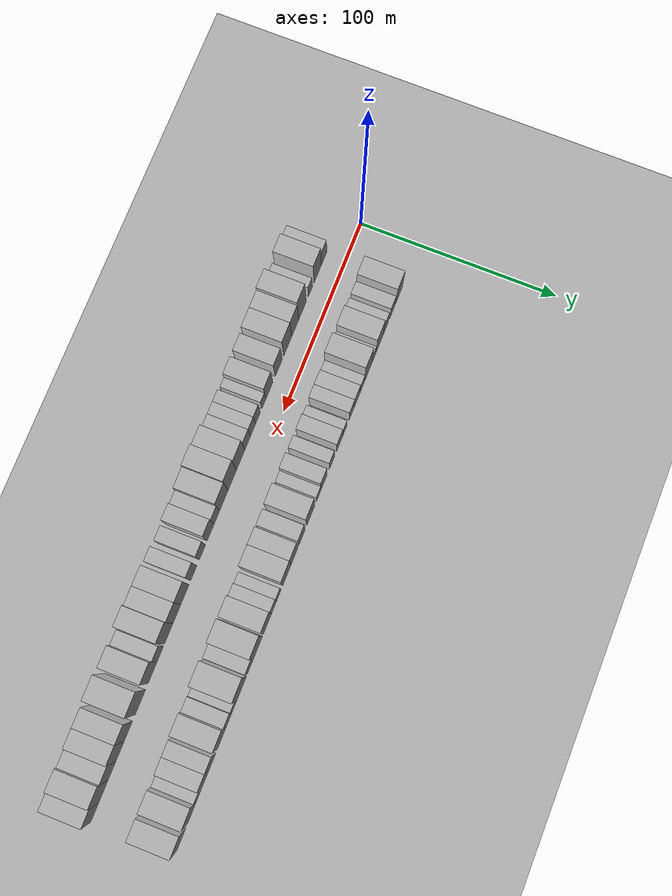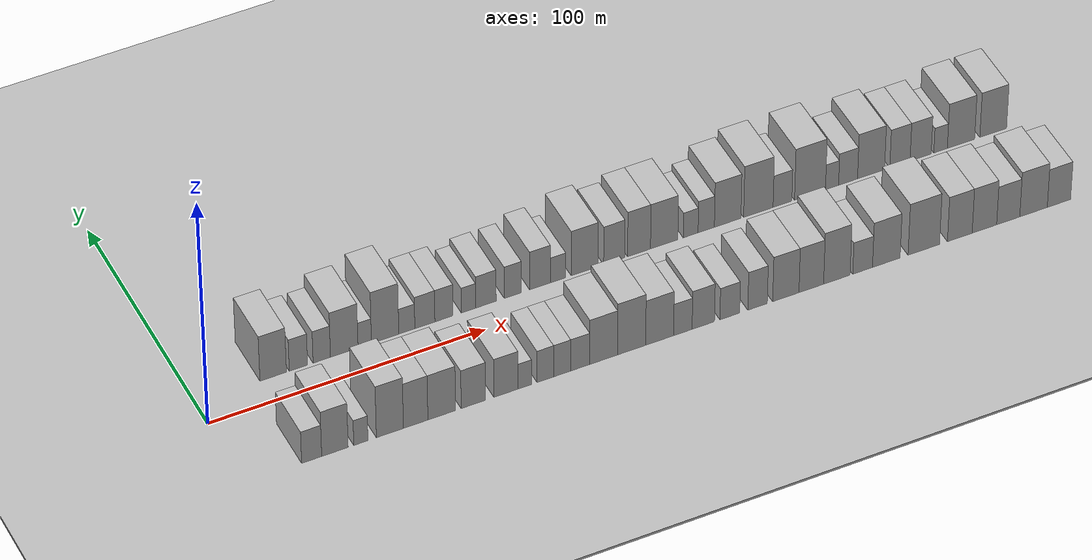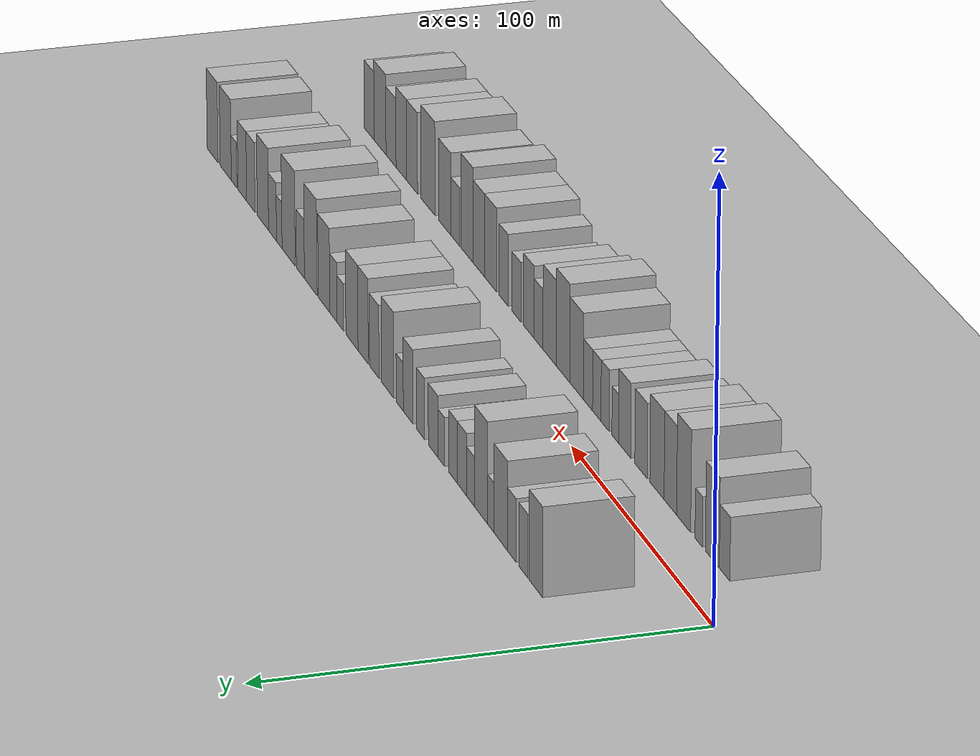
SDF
<?xml version="1.0" encoding="utf-8"?>

<sdf version="1.6">

   <world name="default">

      <gui fullscreen="0">

         <camera name="user_camera">

            <pose>-15 0 4.57585 0 0 0</pose>

            <view_controller>orbit</view_controller>

         </camera>

      </gui>

      <scene>

         <sky>

           <clouds>

             <speed>12</speed>

           </clouds>

         </sky>

         <ambient>0.4 0.4 0.4 1</ambient>

         <background>0.7 0.7 0.7 1</background>

         <shadows>1</shadows>

      </scene>

      <gravity>0 0 -9.8066</gravity>

      <magnetic_field>6e-06 2.3e-05 -4.2e-05</magnetic_field>

      <physics default="0" name="default_physics" type="ode">

         <ode>

            <solver>

               <type>quick</type>

               <iters>10</iters>

               <sor>1.0</sor>

               <use_dynamic_moi_rescaling>0</use_dynamic_moi_rescaling>

            </solver>

            <constraints>

               <cfm>0</cfm>

               <erp>0.2</erp>

               <contact_max_correcting_vel>100</contact_max_correcting_vel>

               <contact_surface_layer>0.001</contact_surface_layer>

            </constraints>

         </ode>

         <max_step_size>0.004</max_step_size>

         <real_time_factor>1</real_time_factor>

         <real_time_update_rate>250</real_time_update_rate>

      </physics>

      <light name="sun" type="directional">

         <cast_shadows>1</cast_shadows>

         <pose>0 0 10 0 0 0</pose>

         <diffuse>0.8 0.8 0.8 1</diffuse>

         <specular>0.2 0.2 0.2 1</specular>

         <attenuation>

            <range>1000</range>

            <constant>0.9</constant>

            <linear>0.01</linear>

            <quadratic>0.001</quadratic>

         </attenuation>

         <direction>-0.5 0.1 -0.9</direction>

      </light>

      <include>

         <name>ground_plane_1</name>

         <uri>model://HANNAS_ground_plane</uri>

         <pose>0 0 0  0 0 0</pose>

      </include>

      <include>

         <name>ground_plane_2</name>

         <uri>model://HANNAS_ground_plane</uri>

         <pose>100 0 0  0 0 0</pose>

      </include>

      <model name="building_1">

         <static>1</static>

         <pose frame="">27.7572 20.0000 0 0.000000 0.000000 1.570796</pose>

         <link name="link">

            <pose frame="">0 0 10.50 0 0 0</pose>

            <collision name="collision">

               <geometry>

                  <box>

                     <size>20.0000 9.5144 21.0000</size>

                  </box>

               </geometry>

               <max_contacts>10</max_contacts>

               <surface>

                  <contact>

                     <ode/>

                  </contact>

                  <bounce/>

                  <friction>

                     <torsional>

                        <ode/>

                     </torsional>

                     <ode/>

                  </friction>

               </surface>

            </collision>

            <visual name="visual">

               <cast_shadows>0</cast_shadows>

               <geometry>

                  <box>

                     <size>20.0000 9.5144 21.0000</size>

                  </box>

               </geometry>

               <material>

                  <script>

                     <uri>model://HANNAS_wall/materials/scripts</uri>

                     <uri>model://HANNAS_wall/materials/textures</uri>

                     <name>vrc/HANNAS_wall</name>

                  </script>

               </material>

            </visual>

            <self_collide>0</self_collide>

            <enable_wind>0</enable_wind>

            <kinematic>0</kinematic>

         </link>

      </model>

      <model name="building_2">

         <static>1</static>

         <pose frame="">36.8097 20.0000 0 0.000000 0.000000 1.570796</pose>

         <link name="link">

            <pose frame="">0 0 7.50 0 0 0</pose>

            <collision name="collision">

               <geometry>

                  <box>

                     <size>20.0000 6.5906 15.0000</size>

                  </box>

               </geometry>

               <max_contacts>10</max_contacts>

               <surface>

                  <contact>

                     <ode/>

                  </contact>

                  <bounce/>

                  <friction>

                     <torsional>

                        <ode/>

                     </torsional>

                     <ode/>

                  </friction>

               </surface>

            </collision>

            <visual name="visual">

               <cast_shadows>0</cast_shadows>

               <geometry>

                  <box>

                     <size>20.0000 6.5906 15.0000</size>

                  </box>

               </geometry>

               <material>

                  <script>

                     <uri>model://HANNAS_wall/materials/scripts</uri>

                     <uri>model://HANNAS_wall/materials/textures</uri>

                     <name>vrc/HANNAS_wall</name>

                  </script>

               </material>

            </visual>

            <self_collide>0</self_collide>

            <enable_wind>0</enable_wind>

            <kinematic>0</kinematic>

         </link>

      </model>

      <model name="building_3">

         <static>1</static>

         <pose frame="">45.2321 20.0000 0 0.000000 0.000000 1.570796</pose>

         <link name="link">

            <pose frame="">0 0 7.50 0 0 0</pose>

            <collision name="collision">

               <geometry>

                  <box>

                     <size>20.0000 6.2540 15.0000</size>

                  </box>

               </geometry>

               <max_contacts>10</max_contacts>

               <surface>

                  <contact>

                     <ode/>

                  </contact>

                  <bounce/>

                  <friction>

                     <torsional>

                        <ode/>

                     </torsional>

                     <ode/>

                  </friction>

               </surface>

            </collision>

            <visual name="visual">

               <cast_shadows>0</cast_shadows>

               <geometry>

                  <box>

                     <size>20.0000 6.2540 15.0000</size>

                  </box>

               </geometry>

               <material>

                  <script>

                     <uri>model://HANNAS_wall/materials/scripts</uri>

                     <uri>model://HANNAS_wall/materials/textures</uri>

                     <name>vrc/HANNAS_wall</name>

                  </script>

               </material>

            </visual>

            <self_collide>0</self_collide>

            <enable_wind>0</enable_wind>

            <kinematic>0</kinematic>

         </link>

      </model>

      <model name="building_4">

         <static>1</static>

         <pose frame="">53.3386 20.0000 0 0.000000 0.000000 1.570796</pose>

         <link name="link">

            <pose frame="">0 0 10.50 0 0 0</pose>

            <collision name="collision">

               <geometry>

                  <box>

                     <size>20.0000 9.9590 21.0000</size>

                  </box>

               </geometry>

               <max_contacts>10</max_contacts>

               <surface>

                  <contact>

                     <ode/>

                  </contact>

                  <bounce/>

                  <friction>

                     <torsional>

                        <ode/>

                     </torsional>

                     <ode/>

                  </friction>

               </surface>

            </collision>

            <visual name="visual">

               <cast_shadows>0</cast_shadows>

               <geometry>

                  <box>

                     <size>20.0000 9.9590 21.0000</size>

                  </box>

               </geometry>

               <material>

                  <script>

                     <uri>model://HANNAS_wall/materials/scripts</uri>

                     <uri>model://HANNAS_wall/materials/textures</uri>

                     <name>vrc/HANNAS_wall</name>

                  </script>

               </material>

            </visual>

            <self_collide>0</self_collide>

            <enable_wind>0</enable_wind>

            <kinematic>0</kinematic>

         </link>

      </model>

      <model name="building_5">

         <static>1</static>

         <pose frame="">60.7465 20.0000 0 0.000000 0.000000 1.570796</pose>

         <link name="link">

            <pose frame="">0 0 6.00 0 0 0</pose>

            <collision name="collision">

               <geometry>

                  <box>

                     <size>20.0000 4.8570 12.0000</size>

                  </box>

               </geometry>

               <max_contacts>10</max_contacts>

               <surface>

                  <contact>

                     <ode/>

                  </contact>

                  <bounce/>

                  <friction>

                     <torsional>

                        <ode/>

                     </torsional>

                     <ode/>

                  </friction>

               </surface>

            </collision>

            <visual name="visual">

               <cast_shadows>0</cast_shadows>

               <geometry>

                  <box>

                     <size>20.0000 4.8570 12.0000</size>

                  </box>

               </geometry>

               <material>

                  <script>

                     <uri>model://HANNAS_wall/materials/scripts</uri>

                     <uri>model://HANNAS_wall/materials/textures</uri>

                     <name>vrc/HANNAS_wall</name>

                  </script>

               </material>

            </visual>

            <self_collide>0</self_collide>

            <enable_wind>0</enable_wind>

            <kinematic>0</kinematic>

         </link>

      </model>

      <model name="building_6">

         <static>1</static>

         <pose frame="">68.1376 20.0000 0 0.000000 0.000000 1.570796</pose>

         <link name="link">

            <pose frame="">0 0 12.00 0 0 0</pose>

            <collision name="collision">

               <geometry>

                  <box>

                     <size>20.0000 9.9251 24.0000</size>

                  </box>

               </geometry>

               <max_contacts>10</max_contacts>

               <surface>

                  <contact>

                     <ode/>

                  </contact>

                  <bounce/>

                  <friction>

                     <torsional>

                        <ode/>

                     </torsional>

                     <ode/>

                  </friction>

               </surface>

            </collision>

            <visual name="visual">

               <cast_shadows>0</cast_shadows>

               <geometry>

                  <box>

                     <size>20.0000 9.9251 24.0000</size>

                  </box>

               </geometry>

               <material>

                  <script>

                     <uri>model://HANNAS_wall/materials/scripts</uri>

                     <uri>model://HANNAS_wall/materials/textures</uri>

                     <name>vrc/HANNAS_wall</name>

                  </script>

               </material>

            </visual>

            <self_collide>0</self_collide>

            <enable_wind>0</enable_wind>

            <kinematic>0</kinematic>

         </link>

      </model>

      <model name="building_7">

         <static>1</static>

         <pose frame="">76.0149 20.0000 0 0.000000 0.000000 1.570796</pose>

         <link name="link">

            <pose frame="">0 0 6.00 0 0 0</pose>

            <collision name="collision">

               <geometry>

                  <box>

                     <size>20.0000 5.8294 12.0000</size>

                  </box>

               </geometry>

               <max_contacts>10</max_contacts>

               <surface>

                  <contact>

                     <ode/>

                  </contact>

                  <bounce/>

                  <friction>

                     <torsional>

                        <ode/>

                     </torsional>

                     <ode/>

                  </friction>

               </surface>

            </collision>

            <visual name="visual">

               <cast_shadows>0</cast_shadows>

               <geometry>

                  <box>

                     <size>20.0000 5.8294 12.0000</size>

                  </box>

               </geometry>

               <material>

                  <script>

                     <uri>model://HANNAS_wall/materials/scripts</uri>

                     <uri>model://HANNAS_wall/materials/textures</uri>

                     <name>vrc/HANNAS_wall</name>

                  </script>

               </material>

            </visual>

            <self_collide>0</self_collide>

            <enable_wind>0</enable_wind>

            <kinematic>0</kinematic>

         </link>

      </model>

      <model name="building_8">

         <static>1</static>

         <pose frame="">82.5758 20.0000 0 0.000000 0.000000 1.570796</pose>

         <link name="link">

            <pose frame="">0 0 7.50 0 0 0</pose>

            <collision name="collision">

               <geometry>

                  <box>

                     <size>20.0000 7.2925 15.0000</size>

                  </box>

               </geometry>

               <max_contacts>10</max_contacts>

               <surface>

                  <contact>

                     <ode/>

                  </contact>

                  <bounce/>

                  <friction>

                     <torsional>

                        <ode/>

                     </torsional>

                     <ode/>

                  </friction>

               </surface>

            </collision>

            <visual name="visual">

               <cast_shadows>0</cast_shadows>

               <geometry>

                  <box>

                     <size>20.0000 7.2925 15.0000</size>

                  </box>

               </geometry>

               <material>

                  <script>

                     <uri>model://HANNAS_wall/materials/scripts</uri>

                     <uri>model://HANNAS_wall/materials/textures</uri>

                     <name>vrc/HANNAS_wall</name>

                  </script>

               </material>

            </visual>

            <self_collide>0</self_collide>

            <enable_wind>0</enable_wind>

            <kinematic>0</kinematic>

         </link>

      </model>

      <model name="building_9">

         <static>1</static>

         <pose frame="">89.5353 20.0000 0 0.000000 0.000000 1.570796</pose>

         <link name="link">

            <pose frame="">0 0 7.50 0 0 0</pose>

            <collision name="collision">

               <geometry>

                  <box>

                     <size>20.0000 6.6265 15.0000</size>

                  </box>

               </geometry>

               <max_contacts>10</max_contacts>

               <surface>

                  <contact>

                     <ode/>

                  </contact>

                  <bounce/>

                  <friction>

                     <torsional>

                        <ode/>

                     </torsional>

                     <ode/>

                  </friction>

               </surface>

            </collision>

            <visual name="visual">

               <cast_shadows>0</cast_shadows>

               <geometry>

                  <box>

                     <size>20.0000 6.6265 15.0000</size>

                  </box>

               </geometry>

               <material>

                  <script>

                     <uri>model://HANNAS_wall/materials/scripts</uri>

                     <uri>model://HANNAS_wall/materials/textures</uri>

                     <name>vrc/HANNAS_wall</name>

                  </script>

               </material>

            </visual>

            <self_collide>0</self_collide>

            <enable_wind>0</enable_wind>

            <kinematic>0</kinematic>

         </link>

      </model>

      <model name="building_10">

         <static>1</static>

         <pose frame="">98.4886 20.0000 0 0.000000 0.000000 1.570796</pose>

         <link name="link">

            <pose frame="">0 0 6.00 0 0 0</pose>

            <collision name="collision">

               <geometry>

                  <box>

                     <size>20.0000 5.2801 12.0000</size>

                  </box>

               </geometry>

               <max_contacts>10</max_contacts>

               <surface>

                  <contact>

                     <ode/>

                  </contact>

                  <bounce/>

                  <friction>

                     <torsional>

                        <ode/>

                     </torsional>

                     <ode/>

                  </friction>

               </surface>

            </collision>

            <visual name="visual">

               <cast_shadows>0</cast_shadows>

               <geometry>

                  <box>

                     <size>20.0000 5.2801 12.0000</size>

                  </box>

               </geometry>

               <material>

                  <script>

                     <uri>model://HANNAS_wall/materials/scripts</uri>

                     <uri>model://HANNAS_wall/materials/textures</uri>

                     <name>vrc/HANNAS_wall</name>

                  </script>

               </material>

            </visual>

            <self_collide>0</self_collide>

            <enable_wind>0</enable_wind>

            <kinematic>0</kinematic>

         </link>

      </model>

      <model name="building_11">

         <static>1</static>

         <pose frame="">104.8770 20.0000 0 0.000000 0.000000 1.570796</pose>

         <link name="link">

            <pose frame="">0 0 7.50 0 0 0</pose>

            <collision name="collision">

               <geometry>

                  <box>

                     <size>20.0000 7.4967 15.0000</size>

                  </box>

               </geometry>

               <max_contacts>10</max_contacts>

               <surface>

                  <contact>

                     <ode/>

                  </contact>

                  <bounce/>

                  <friction>

                     <torsional>

                        <ode/>

                     </torsional>

                     <ode/>

                  </friction>

               </surface>

            </collision>

            <visual name="visual">

               <cast_shadows>0</cast_shadows>

               <geometry>

                  <box>

                     <size>20.0000 7.4967 15.0000</size>

                  </box>

               </geometry>

               <material>

                  <script>

                     <uri>model://HANNAS_wall/materials/scripts</uri>

                     <uri>model://HANNAS_wall/materials/textures</uri>

                     <name>vrc/HANNAS_wall</name>

                  </script>

               </material>

            </visual>

            <self_collide>0</self_collide>

            <enable_wind>0</enable_wind>

            <kinematic>0</kinematic>

         </link>

      </model>

      <model name="building_12">

         <static>1</static>

         <pose frame="">114.7740 20.0000 0 0.000000 0.000000 1.570796</pose>

         <link name="link">

            <pose frame="">0 0 7.50 0 0 0</pose>

            <collision name="collision">

               <geometry>

                  <box>

                     <size>20.0000 6.2972 15.0000</size>

                  </box>

               </geometry>

               <max_contacts>10</max_contacts>

               <surface>

                  <contact>

                     <ode/>

                  </contact>

                  <bounce/>

                  <friction>

                     <torsional>

                        <ode/>

                     </torsional>

                     <ode/>

                  </friction>

               </surface>

            </collision>

            <visual name="visual">

               <cast_shadows>0</cast_shadows>

               <geometry>

                  <box>

                     <size>20.0000 6.2972 15.0000</size>

                  </box>

               </geometry>

               <material>

                  <script>

                     <uri>model://HANNAS_wall/materials/scripts</uri>

                     <uri>model://HANNAS_wall/materials/textures</uri>

                     <name>vrc/HANNAS_wall</name>

                  </script>

               </material>

            </visual>

            <self_collide>0</self_collide>

            <enable_wind>0</enable_wind>

            <kinematic>0</kinematic>

         </link>

      </model>

      <model name="building_13">

         <static>1</static>

         <pose frame="">124.7443 20.0000 0 0.000000 0.000000 1.570796</pose>

         <link name="link">

            <pose frame="">0 0 9.00 0 0 0</pose>

            <collision name="collision">

               <geometry>

                  <box>

                     <size>20.0000 7.6435 18.0000</size>

                  </box>

               </geometry>

               <max_contacts>10</max_contacts>

               <surface>

                  <contact>

                     <ode/>

                  </contact>

                  <bounce/>

                  <friction>

                     <torsional>

                        <ode/>

                     </torsional>

                     <ode/>

                  </friction>

               </surface>

            </collision>

            <visual name="visual">

               <cast_shadows>0</cast_shadows>

               <geometry>

                  <box>

                     <size>20.0000 7.6435 18.0000</size>

                  </box>

               </geometry>

               <material>

                  <script>

                     <uri>model://HANNAS_wall/materials/scripts</uri>

                     <uri>model://HANNAS_wall/materials/textures</uri>

                     <name>vrc/HANNAS_wall</name>

                  </script>

               </material>

            </visual>

            <self_collide>0</self_collide>

            <enable_wind>0</enable_wind>

            <kinematic>0</kinematic>

         </link>

      </model>

      <model name="building_14">

         <static>1</static>

         <pose frame="">131.4072 20.0000 0 0.000000 0.000000 1.570796</pose>

         <link name="link">

            <pose frame="">0 0 6.00 0 0 0</pose>

            <collision name="collision">

               <geometry>

                  <box>

                     <size>20.0000 5.6821 12.0000</size>

                  </box>

               </geometry>

               <max_contacts>10</max_contacts>

               <surface>

                  <contact>

                     <ode/>

                  </contact>

                  <bounce/>

                  <friction>

                     <torsional>

                        <ode/>

                     </torsional>

                     <ode/>

                  </friction>

               </surface>

            </collision>

            <visual name="visual">

               <cast_shadows>0</cast_shadows>

               <geometry>

                  <box>

                     <size>20.0000 5.6821 12.0000</size>

                  </box>

               </geometry>

               <material>

                  <script>

                     <uri>model://HANNAS_wall/materials/scripts</uri>

                     <uri>model://HANNAS_wall/materials/textures</uri>

                     <name>vrc/HANNAS_wall</name>

                  </script>

               </material>

            </visual>

            <self_collide>0</self_collide>

            <enable_wind>0</enable_wind>

            <kinematic>0</kinematic>

         </link>

      </model>

      <model name="building_15">

         <static>1</static>

         <pose frame="">141.2418 20.0000 0 0.000000 0.000000 1.570796</pose>

         <link name="link">

            <pose frame="">0 0 10.50 0 0 0</pose>

            <collision name="collision">

               <geometry>

                  <box>

                     <size>20.0000 9.9872 21.0000</size>

                  </box>

               </geometry>

               <max_contacts>10</max_contacts>

               <surface>

                  <contact>

                     <ode/>

                  </contact>

                  <bounce/>

                  <friction>

                     <torsional>

                        <ode/>

                     </torsional>

                     <ode/>

                  </friction>

               </surface>

            </collision>

            <visual name="visual">

               <cast_shadows>0</cast_shadows>

               <geometry>

                  <box>

                     <size>20.0000 9.9872 21.0000</size>

                  </box>

               </geometry>

               <material>

                  <script>

                     <uri>model://HANNAS_wall/materials/scripts</uri>

                     <uri>model://HANNAS_wall/materials/textures</uri>

                     <name>vrc/HANNAS_wall</name>

                  </script>

               </material>

            </visual>

            <self_collide>0</self_collide>

            <enable_wind>0</enable_wind>

            <kinematic>0</kinematic>

         </link>

      </model>

      <model name="building_16">

         <static>1</static>

         <pose frame="">152.1717 20.0000 0 0.000000 0.000000 1.570796</pose>

         <link name="link">

            <pose frame="">0 0 9.00 0 0 0</pose>

            <collision name="collision">

               <geometry>

                  <box>

                     <size>20.0000 7.8726 18.0000</size>

                  </box>

               </geometry>

               <max_contacts>10</max_contacts>

               <surface>

                  <contact>

                     <ode/>

                  </contact>

                  <bounce/>

                  <friction>

                     <torsional>

                        <ode/>

                     </torsional>

                     <ode/>

                  </friction>

               </surface>

            </collision>

            <visual name="visual">

               <cast_shadows>0</cast_shadows>

               <geometry>

                  <box>

                     <size>20.0000 7.8726 18.0000</size>

                  </box>

               </geometry>

               <material>

                  <script>

                     <uri>model://HANNAS_wall/materials/scripts</uri>

                     <uri>model://HANNAS_wall/materials/textures</uri>

                     <name>vrc/HANNAS_wall</name>

                  </script>

               </material>

            </visual>

            <self_collide>0</self_collide>

            <enable_wind>0</enable_wind>

            <kinematic>0</kinematic>

         </link>

      </model>

      <model name="building_17">

         <static>1</static>

         <pose frame="">161.3731 20.0000 0 0.000000 0.000000 1.570796</pose>

         <link name="link">

            <pose frame="">0 0 10.50 0 0 0</pose>

            <collision name="collision">

               <geometry>

                  <box>

                     <size>20.0000 8.5301 21.0000</size>

                  </box>

               </geometry>

               <max_contacts>10</max_contacts>

               <surface>

                  <contact>

                     <ode/>

                  </contact>

                  <bounce/>

                  <friction>

                     <torsional>

                        <ode/>

                     </torsional>

                     <ode/>

                  </friction>

               </surface>

            </collision>

            <visual name="visual">

               <cast_shadows>0</cast_shadows>

               <geometry>

                  <box>

                     <size>20.0000 8.5301 21.0000</size>

                  </box>

               </geometry>

               <material>

                  <script>

                     <uri>model://HANNAS_wall/materials/scripts</uri>

                     <uri>model://HANNAS_wall/materials/textures</uri>

                     <name>vrc/HANNAS_wall</name>

                  </script>

               </material>

            </visual>

            <self_collide>0</self_collide>

            <enable_wind>0</enable_wind>

            <kinematic>0</kinematic>

         </link>

      </model>

      <model name="building_18">

         <static>1</static>

         <pose frame="">170.7369 20.0000 0 0.000000 0.000000 1.570796</pose>

         <link name="link">

            <pose frame="">0 0 10.50 0 0 0</pose>

            <collision name="collision">

               <geometry>

                  <box>

                     <size>20.0000 10.1977 21.0000</size>

                  </box>

               </geometry>

               <max_contacts>10</max_contacts>

               <surface>

                  <contact>

                     <ode/>

                  </contact>

                  <bounce/>

                  <friction>

                     <torsional>

                        <ode/>

                     </torsional>

                     <ode/>

                  </friction>

               </surface>

            </collision>

            <visual name="visual">

               <cast_shadows>0</cast_shadows>

               <geometry>

                  <box>

                     <size>20.0000 10.1977 21.0000</size>

                  </box>

               </geometry>

               <material>

                  <script>

                     <uri>model://HANNAS_wall/materials/scripts</uri>

                     <uri>model://HANNAS_wall/materials/textures</uri>

                     <name>vrc/HANNAS_wall</name>

                  </script>

               </material>

            </visual>

            <self_collide>0</self_collide>

            <enable_wind>0</enable_wind>

            <kinematic>0</kinematic>

         </link>

      </model>

      <model name="building_19">

         <static>1</static>

         <pose frame="">180.6110 20.0000 0 0.000000 0.000000 1.570796</pose>

         <link name="link">

            <pose frame="">0 0 6.00 0 0 0</pose>

            <collision name="collision">

               <geometry>

                  <box>

                     <size>20.0000 5.5505 12.0000</size>

                  </box>

               </geometry>

               <max_contacts>10</max_contacts>

               <surface>

                  <contact>

                     <ode/>

                  </contact>

                  <bounce/>

                  <friction>

                     <torsional>

                        <ode/>

                     </torsional>

                     <ode/>

                  </friction>

               </surface>

            </collision>

            <visual name="visual">

               <cast_shadows>0</cast_shadows>

               <geometry>

                  <box>

                     <size>20.0000 5.5505 12.0000</size>

                  </box>

               </geometry>

               <material>

                  <script>

                     <uri>model://HANNAS_wall/materials/scripts</uri>

                     <uri>model://HANNAS_wall/materials/textures</uri>

                     <name>vrc/HANNAS_wall</name>

                  </script>

               </material>

            </visual>

            <self_collide>0</self_collide>

            <enable_wind>0</enable_wind>

            <kinematic>0</kinematic>

         </link>

      </model>

      <model name="building_20">

         <static>1</static>

         <pose frame="">186.4364 20.0000 0 0.000000 0.000000 1.570796</pose>

         <link name="link">

            <pose frame="">0 0 7.50 0 0 0</pose>

            <collision name="collision">

               <geometry>

                  <box>

                     <size>20.0000 6.1003 15.0000</size>

                  </box>

               </geometry>

               <max_contacts>10</max_contacts>

               <surface>

                  <contact>

                     <ode/>

                  </contact>

                  <bounce/>

                  <friction>

                     <torsional>

                        <ode/>

                     </torsional>

                     <ode/>

                  </friction>

               </surface>

            </collision>

            <visual name="visual">

               <cast_shadows>0</cast_shadows>

               <geometry>

                  <box>

                     <size>20.0000 6.1003 15.0000</size>

                  </box>

               </geometry>

               <material>

                  <script>

                     <uri>model://HANNAS_wall/materials/scripts</uri>

                     <uri>model://HANNAS_wall/materials/textures</uri>

                     <name>vrc/HANNAS_wall</name>

                  </script>

               </material>

            </visual>

            <self_collide>0</self_collide>

            <enable_wind>0</enable_wind>

            <kinematic>0</kinematic>

         </link>

      </model>

      <model name="building_21">

         <static>1</static>

         <pose frame="">194.4654 20.0000 0 0.000000 0.000000 1.570796</pose>

         <link name="link">

            <pose frame="">0 0 10.50 0 0 0</pose>

            <collision name="collision">

               <geometry>

                  <box>

                     <size>20.0000 9.9576 21.0000</size>

                  </box>

               </geometry>

               <max_contacts>10</max_contacts>

               <surface>

                  <contact>

                     <ode/>

                  </contact>

                  <bounce/>

                  <friction>

                     <torsional>

                        <ode/>

                     </torsional>

                     <ode/>

                  </friction>

               </surface>

            </collision>

            <visual name="visual">

               <cast_shadows>0</cast_shadows>

               <geometry>

                  <box>

                     <size>20.0000 9.9576 21.0000</size>

                  </box>

               </geometry>

               <material>

                  <script>

                     <uri>model://HANNAS_wall/materials/scripts</uri>

                     <uri>model://HANNAS_wall/materials/textures</uri>

                     <name>vrc/HANNAS_wall</name>

                  </script>

               </material>

            </visual>

            <self_collide>0</self_collide>

            <enable_wind>0</enable_wind>

            <kinematic>0</kinematic>

         </link>

      </model>

      <model name="building_22">

         <static>1</static>

         <pose frame="">205.9872 20.0000 0 0.000000 0.000000 1.570796</pose>

         <link name="link">

            <pose frame="">0 0 12.00 0 0 0</pose>

            <collision name="collision">

               <geometry>

                  <box>

                     <size>20.0000 11.0861 24.0000</size>

                  </box>

               </geometry>

               <max_contacts>10</max_contacts>

               <surface>

                  <contact>

                     <ode/>

                  </contact>

                  <bounce/>

                  <friction>

                     <torsional>

                        <ode/>

                     </torsional>

                     <ode/>

                  </friction>

               </surface>

            </collision>

            <visual name="visual">

               <cast_shadows>0</cast_shadows>

               <geometry>

                  <box>

                     <size>20.0000 11.0861 24.0000</size>

                  </box>

               </geometry>

               <material>

                  <script>

                     <uri>model://HANNAS_wall/materials/scripts</uri>

                     <uri>model://HANNAS_wall/materials/textures</uri>

                     <name>vrc/HANNAS_wall</name>

                  </script>

               </material>

            </visual>

            <self_collide>0</self_collide>

            <enable_wind>0</enable_wind>

            <kinematic>0</kinematic>

         </link>

      </model>

      <model name="building_23">

         <static>1</static>

         <pose frame="">215.0701 20.0000 0 0.000000 0.000000 1.570796</pose>

         <link name="link">

            <pose frame="">0 0 7.50 0 0 0</pose>

            <collision name="collision">

               <geometry>

                  <box>

                     <size>20.0000 7.0795 15.0000</size>

                  </box>

               </geometry>

               <max_contacts>10</max_contacts>

               <surface>

                  <contact>

                     <ode/>

                  </contact>

                  <bounce/>

                  <friction>

                     <torsional>

                        <ode/>

                     </torsional>

                     <ode/>

                  </friction>

               </surface>

            </collision>

            <visual name="visual">

               <cast_shadows>0</cast_shadows>

               <geometry>

                  <box>

                     <size>20.0000 7.0795 15.0000</size>

                  </box>

               </geometry>

               <material>

                  <script>

                     <uri>model://HANNAS_wall/materials/scripts</uri>

                     <uri>model://HANNAS_wall/materials/textures</uri>

                     <name>vrc/HANNAS_wall</name>

                  </script>

               </material>

            </visual>

            <self_collide>0</self_collide>

            <enable_wind>0</enable_wind>

            <kinematic>0</kinematic>

         </link>

      </model>

      <model name="building_24">

         <static>1</static>

         <pose frame="">225.4711 20.0000 0 0.000000 0.000000 1.570796</pose>

         <link name="link">

            <pose frame="">0 0 12.00 0 0 0</pose>

            <collision name="collision">

               <geometry>

                  <box>

                     <size>20.0000 11.7225 24.0000</size>

                  </box>

               </geometry>

               <max_contacts>10</max_contacts>

               <surface>

                  <contact>

                     <ode/>

                  </contact>

                  <bounce/>

                  <friction>

                     <torsional>

                        <ode/>

                     </torsional>

                     <ode/>

                  </friction>

               </surface>

            </collision>

            <visual name="visual">

               <cast_shadows>0</cast_shadows>

               <geometry>

                  <box>

                     <size>20.0000 11.7225 24.0000</size>

                  </box>

               </geometry>

               <material>

                  <script>

                     <uri>model://HANNAS_wall/materials/scripts</uri>

                     <uri>model://HANNAS_wall/materials/textures</uri>

                     <name>vrc/HANNAS_wall</name>

                  </script>

               </material>

            </visual>

            <self_collide>0</self_collide>

            <enable_wind>0</enable_wind>

            <kinematic>0</kinematic>

         </link>

      </model>

      <model name="building_25">

         <static>1</static>

         <pose frame="">233.8151 20.0000 0 0.000000 0.000000 1.570796</pose>

         <link name="link">

            <pose frame="">0 0 6.00 0 0 0</pose>

            <collision name="collision">

               <geometry>

                  <box>

                     <size>20.0000 4.9655 12.0000</size>

                  </box>

               </geometry>

               <max_contacts>10</max_contacts>

               <surface>

                  <contact>

                     <ode/>

                  </contact>

                  <bounce/>

                  <friction>

                     <torsional>

                        <ode/>

                     </torsional>

                     <ode/>

                  </friction>

               </surface>

            </collision>

            <visual name="visual">

               <cast_shadows>0</cast_shadows>

               <geometry>

                  <box>

                     <size>20.0000 4.9655 12.0000</size>

                  </box>

               </geometry>

               <material>

                  <script>

                     <uri>model://HANNAS_wall/materials/scripts</uri>

                     <uri>model://HANNAS_wall/materials/textures</uri>

                     <name>vrc/HANNAS_wall</name>

                  </script>

               </material>

            </visual>

            <self_collide>0</self_collide>

            <enable_wind>0</enable_wind>

            <kinematic>0</kinematic>

         </link>

      </model>

      <model name="building_26">

         <static>1</static>

         <pose frame="">239.8933 20.0000 0 0.000000 0.000000 1.570796</pose>

         <link name="link">

            <pose frame="">0 0 7.50 0 0 0</pose>

            <collision name="collision">

               <geometry>

                  <box>

                     <size>20.0000 7.1910 15.0000</size>

                  </box>

               </geometry>

               <max_contacts>10</max_contacts>

               <surface>

                  <contact>

                     <ode/>

                  </contact>

                  <bounce/>

                  <friction>

                     <torsional>

                        <ode/>

                     </torsional>

                     <ode/>

                  </friction>

               </surface>

            </collision>

            <visual name="visual">

               <cast_shadows>0</cast_shadows>

               <geometry>

                  <box>

                     <size>20.0000 7.1910 15.0000</size>

                  </box>

               </geometry>

               <material>

                  <script>

                     <uri>model://HANNAS_wall/materials/scripts</uri>

                     <uri>model://HANNAS_wall/materials/textures</uri>

                     <name>vrc/HANNAS_wall</name>

                  </script>

               </material>

            </visual>

            <self_collide>0</self_collide>

            <enable_wind>0</enable_wind>

            <kinematic>0</kinematic>

         </link>

      </model>

      <model name="building_27">

         <static>1</static>

         <pose frame="">248.6261 20.0000 0 0.000000 0.000000 1.570796</pose>

         <link name="link">

            <pose frame="">0 0 10.50 0 0 0</pose>

            <collision name="collision">

               <geometry>

                  <box>

                     <size>20.0000 10.2746 21.0000</size>

                  </box>

               </geometry>

               <max_contacts>10</max_contacts>

               <surface>

                  <contact>

                     <ode/>

                  </contact>

                  <bounce/>

                  <friction>

                     <torsional>

                        <ode/>

                     </torsional>

                     <ode/>

                  </friction>

               </surface>

            </collision>

            <visual name="visual">

               <cast_shadows>0</cast_shadows>

               <geometry>

                  <box>

                     <size>20.0000 10.2746 21.0000</size>

                  </box>

               </geometry>

               <material>

                  <script>

                     <uri>model://HANNAS_wall/materials/scripts</uri>

                     <uri>model://HANNAS_wall/materials/textures</uri>

                     <name>vrc/HANNAS_wall</name>

                  </script>

               </material>

            </visual>

            <self_collide>0</self_collide>

            <enable_wind>0</enable_wind>

            <kinematic>0</kinematic>

         </link>

      </model>

      <model name="building_28">

         <static>1</static>

         <pose frame="">259.6235 20.0000 0 0.000000 0.000000 1.570796</pose>

         <link name="link">

            <pose frame="">0 0 9.00 0 0 0</pose>

            <collision name="collision">

               <geometry>

                  <box>

                     <size>20.0000 7.7201 18.0000</size>

                  </box>

               </geometry>

               <max_contacts>10</max_contacts>

               <surface>

                  <contact>

                     <ode/>

                  </contact>

                  <bounce/>

                  <friction>

                     <torsional>

                        <ode/>

                     </torsional>

                     <ode/>

                  </friction>

               </surface>

            </collision>

            <visual name="visual">

               <cast_shadows>0</cast_shadows>

               <geometry>

                  <box>

                     <size>20.0000 7.7201 18.0000</size>

                  </box>

               </geometry>

               <material>

                  <script>

                     <uri>model://HANNAS_wall/materials/scripts</uri>

                     <uri>model://HANNAS_wall/materials/textures</uri>

                     <name>vrc/HANNAS_wall</name>

                  </script>

               </material>

            </visual>

            <self_collide>0</self_collide>

            <enable_wind>0</enable_wind>

            <kinematic>0</kinematic>

         </link>

      </model>

      <model name="building_29">

         <static>1</static>

         <pose frame="">267.5244 20.0000 0 0.000000 0.000000 1.570796</pose>

         <link name="link">

            <pose frame="">0 0 9.00 0 0 0</pose>

            <collision name="collision">

               <geometry>

                  <box>

                     <size>20.0000 8.0817 18.0000</size>

                  </box>

               </geometry>

               <max_contacts>10</max_contacts>

               <surface>

                  <contact>

                     <ode/>

                  </contact>

                  <bounce/>

                  <friction>

                     <torsional>

                        <ode/>

                     </torsional>

                     <ode/>

                  </friction>

               </surface>

            </collision>

            <visual name="visual">

               <cast_shadows>0</cast_shadows>

               <geometry>

                  <box>

                     <size>20.0000 8.0817 18.0000</size>

                  </box>

               </geometry>

               <material>

                  <script>

                     <uri>model://HANNAS_wall/materials/scripts</uri>

                     <uri>model://HANNAS_wall/materials/textures</uri>

                     <name>vrc/HANNAS_wall</name>

                  </script>

               </material>

            </visual>

            <self_collide>0</self_collide>

            <enable_wind>0</enable_wind>

            <kinematic>0</kinematic>

         </link>

      </model>

      <model name="building_30">

         <static>1</static>

         <pose frame="">275.1618 20.0000 0 0.000000 0.000000 1.570796</pose>

         <link name="link">

            <pose frame="">0 0 6.00 0 0 0</pose>

            <collision name="collision">

               <geometry>

                  <box>

                     <size>20.0000 5.1931 12.0000</size>

                  </box>

               </geometry>

               <max_contacts>10</max_contacts>

               <surface>

                  <contact>

                     <ode/>

                  </contact>

                  <bounce/>

                  <friction>

                     <torsional>

                        <ode/>

                     </torsional>

                     <ode/>

                  </friction>

               </surface>

            </collision>

            <visual name="visual">

               <cast_shadows>0</cast_shadows>

               <geometry>

                  <box>

                     <size>20.0000 5.1931 12.0000</size>

                  </box>

               </geometry>

               <material>

                  <script>

                     <uri>model://HANNAS_wall/materials/scripts</uri>

                     <uri>model://HANNAS_wall/materials/textures</uri>

                     <name>vrc/HANNAS_wall</name>

                  </script>

               </material>

            </visual>

            <self_collide>0</self_collide>

            <enable_wind>0</enable_wind>

            <kinematic>0</kinematic>

         </link>

      </model>

      <model name="building_31">

         <static>1</static>

         <pose frame="">282.9923 20.0000 0 0.000000 0.000000 1.570796</pose>

         <link name="link">

            <pose frame="">0 0 10.50 0 0 0</pose>

            <collision name="collision">

               <geometry>

                  <box>

                     <size>20.0000 10.4677 21.0000</size>

                  </box>

               </geometry>

               <max_contacts>10</max_contacts>

               <surface>

                  <contact>

                     <ode/>

                  </contact>

                  <bounce/>

                  <friction>

                     <torsional>

                        <ode/>

                     </torsional>

                     <ode/>

                  </friction>

               </surface>

            </collision>

            <visual name="visual">

               <cast_shadows>0</cast_shadows>

               <geometry>

                  <box>

                     <size>20.0000 10.4677 21.0000</size>

                  </box>

               </geometry>

               <material>

                  <script>

                     <uri>model://HANNAS_wall/materials/scripts</uri>

                     <uri>model://HANNAS_wall/materials/textures</uri>

                     <name>vrc/HANNAS_wall</name>

                  </script>

               </material>

            </visual>

            <self_collide>0</self_collide>

            <enable_wind>0</enable_wind>

            <kinematic>0</kinematic>

         </link>

      </model>

      <model name="building_32">

         <static>1</static>

         <pose frame="">295.3724 20.0000 0 0.000000 0.000000 1.570796</pose>

         <link name="link">

            <pose frame="">0 0 10.50 0 0 0</pose>

            <collision name="collision">

               <geometry>

                  <box>

                     <size>20.0000 10.2925 21.0000</size>

                  </box>

               </geometry>

               <max_contacts>10</max_contacts>

               <surface>

                  <contact>

                     <ode/>

                  </contact>

                  <bounce/>

                  <friction>

                     <torsional>

                        <ode/>

                     </torsional>

                     <ode/>

                  </friction>

               </surface>

            </collision>

            <visual name="visual">

               <cast_shadows>0</cast_shadows>

               <geometry>

                  <box>

                     <size>20.0000 10.2925 21.0000</size>

                  </box>

               </geometry>

               <material>

                  <script>

                     <uri>model://HANNAS_wall/materials/scripts</uri>

                     <uri>model://HANNAS_wall/materials/textures</uri>

                     <name>vrc/HANNAS_wall</name>

                  </script>

               </material>

            </visual>

            <self_collide>0</self_collide>

            <enable_wind>0</enable_wind>

            <kinematic>0</kinematic>

         </link>

      </model>

      <model name="building_33">

         <static>1</static>

         <pose frame="">23.5636 -20.0000 0 0.000000 0.000000 1.570796</pose>

         <link name="link">

            <pose frame="">0 0 7.50 0 0 0</pose>

            <collision name="collision">

               <geometry>

                  <box>

                     <size>20.0000 7.1272 15.0000</size>

                  </box>

               </geometry>

               <max_contacts>10</max_contacts>

               <surface>

                  <contact>

                     <ode/>

                  </contact>

                  <bounce/>

                  <friction>

                     <torsional>

                        <ode/>

                     </torsional>

                     <ode/>

                  </friction>

               </surface>

            </collision>

            <visual name="visual">

               <cast_shadows>0</cast_shadows>

               <geometry>

                  <box>

                     <size>20.0000 7.1272 15.0000</size>

                  </box>

               </geometry>

               <material>

                  <script>

                     <uri>model://HANNAS_wall/materials/scripts</uri>

                     <uri>model://HANNAS_wall/materials/textures</uri>

                     <name>vrc/HANNAS_wall</name>

                  </script>

               </material>

            </visual>

            <self_collide>0</self_collide>

            <enable_wind>0</enable_wind>

            <kinematic>0</kinematic>

         </link>

      </model>

      <model name="building_34">

         <static>1</static>

         <pose frame="">31.8367 -20.0000 0 0.000000 0.000000 1.570796</pose>

         <link name="link">

            <pose frame="">0 0 10.50 0 0 0</pose>

            <collision name="collision">

               <geometry>

                  <box>

                     <size>20.0000 9.4190 21.0000</size>

                  </box>

               </geometry>

               <max_contacts>10</max_contacts>

               <surface>

                  <contact>

                     <ode/>

                  </contact>

                  <bounce/>

                  <friction>

                     <torsional>

                        <ode/>

                     </torsional>

                     <ode/>

                  </friction>

               </surface>

            </collision>

            <visual name="visual">

               <cast_shadows>0</cast_shadows>

               <geometry>

                  <box>

                     <size>20.0000 9.4190 21.0000</size>

                  </box>

               </geometry>

               <material>

                  <script>

                     <uri>model://HANNAS_wall/materials/scripts</uri>

                     <uri>model://HANNAS_wall/materials/textures</uri>

                     <name>vrc/HANNAS_wall</name>

                  </script>

               </material>

            </visual>

            <self_collide>0</self_collide>

            <enable_wind>0</enable_wind>

            <kinematic>0</kinematic>

         </link>

      </model>

      <model name="building_35">

         <static>1</static>

         <pose frame="">41.0851 -20.0000 0 0.000000 0.000000 1.570796</pose>

         <link name="link">

            <pose frame="">0 0 6.00 0 0 0</pose>

            <collision name="collision">

               <geometry>

                  <box>

                     <size>20.0000 5.0776 12.0000</size>

                  </box>

               </geometry>

               <max_contacts>10</max_contacts>

               <surface>

                  <contact>

                     <ode/>

                  </contact>

                  <bounce/>

                  <friction>

                     <torsional>

                        <ode/>

                     </torsional>

                     <ode/>

                  </friction>

               </surface>

            </collision>

            <visual name="visual">

               <cast_shadows>0</cast_shadows>

               <geometry>

                  <box>

                     <size>20.0000 5.0776 12.0000</size>

                  </box>

               </geometry>

               <material>

                  <script>

                     <uri>model://HANNAS_wall/materials/scripts</uri>

                     <uri>model://HANNAS_wall/materials/textures</uri>

                     <name>vrc/HANNAS_wall</name>

                  </script>

               </material>

            </visual>

            <self_collide>0</self_collide>

            <enable_wind>0</enable_wind>

            <kinematic>0</kinematic>

         </link>

      </model>

      <model name="building_36">

         <static>1</static>

         <pose frame="">51.4706 -20.0000 0 0.000000 0.000000 1.570796</pose>

         <link name="link">

            <pose frame="">0 0 12.00 0 0 0</pose>

            <collision name="collision">

               <geometry>

                  <box>

                     <size>20.0000 9.6934 24.0000</size>

                  </box>

               </geometry>

               <max_contacts>10</max_contacts>

               <surface>

                  <contact>

                     <ode/>

                  </contact>

                  <bounce/>

                  <friction>

                     <torsional>

                        <ode/>

                     </torsional>

                     <ode/>

                  </friction>

               </surface>

            </collision>

            <visual name="visual">

               <cast_shadows>0</cast_shadows>

               <geometry>

                  <box>

                     <size>20.0000 9.6934 24.0000</size>

                  </box>

               </geometry>

               <material>

                  <script>

                     <uri>model://HANNAS_wall/materials/scripts</uri>

                     <uri>model://HANNAS_wall/materials/textures</uri>

                     <name>vrc/HANNAS_wall</name>

                  </script>

               </material>

            </visual>

            <self_collide>0</self_collide>

            <enable_wind>0</enable_wind>

            <kinematic>0</kinematic>

         </link>

      </model>

      <model name="building_37">

         <static>1</static>

         <pose frame="">60.7078 -20.0000 0 0.000000 0.000000 1.570796</pose>

         <link name="link">

            <pose frame="">0 0 10.50 0 0 0</pose>

            <collision name="collision">

               <geometry>

                  <box>

                     <size>20.0000 8.7810 21.0000</size>

                  </box>

               </geometry>

               <max_contacts>10</max_contacts>

               <surface>

                  <contact>

                     <ode/>

                  </contact>

                  <bounce/>

                  <friction>

                     <torsional>

                        <ode/>

                     </torsional>

                     <ode/>

                  </friction>

               </surface>

            </collision>

            <visual name="visual">

               <cast_shadows>0</cast_shadows>

               <geometry>

                  <box>

                     <size>20.0000 8.7810 21.0000</size>

                  </box>

               </geometry>

               <material>

                  <script>

                     <uri>model://HANNAS_wall/materials/scripts</uri>

                     <uri>model://HANNAS_wall/materials/textures</uri>

                     <name>vrc/HANNAS_wall</name>

                  </script>

               </material>

            </visual>

            <self_collide>0</self_collide>

            <enable_wind>0</enable_wind>

            <kinematic>0</kinematic>

         </link>

      </model>

      <model name="building_38">

         <static>1</static>

         <pose frame="">70.0884 -20.0000 0 0.000000 0.000000 1.570796</pose>

         <link name="link">

            <pose frame="">0 0 10.50 0 0 0</pose>

            <collision name="collision">

               <geometry>

                  <box>

                     <size>20.0000 9.9802 21.0000</size>

                  </box>

               </geometry>

               <max_contacts>10</max_contacts>

               <surface>

                  <contact>

                     <ode/>

                  </contact>

                  <bounce/>

                  <friction>

                     <torsional>

                        <ode/>

                     </torsional>

                     <ode/>

                  </friction>

               </surface>

            </collision>

            <visual name="visual">

               <cast_shadows>0</cast_shadows>

               <geometry>

                  <box>

                     <size>20.0000 9.9802 21.0000</size>

                  </box>

               </geometry>

               <material>

                  <script>

                     <uri>model://HANNAS_wall/materials/scripts</uri>

                     <uri>model://HANNAS_wall/materials/textures</uri>

                     <name>vrc/HANNAS_wall</name>

                  </script>

               </material>

            </visual>

            <self_collide>0</self_collide>

            <enable_wind>0</enable_wind>

            <kinematic>0</kinematic>

         </link>

      </model>

      <model name="building_39">

         <static>1</static>

         <pose frame="">81.4839 -20.0000 0 0.000000 0.000000 1.570796</pose>

         <link name="link">

            <pose frame="">0 0 9.00 0 0 0</pose>

            <collision name="collision">

               <geometry>

                  <box>

                     <size>20.0000 8.8109 18.0000</size>

                  </box>

               </geometry>

               <max_contacts>10</max_contacts>

               <surface>

                  <contact>

                     <ode/>

                  </contact>

                  <bounce/>

                  <friction>

                     <torsional>

                        <ode/>

                     </torsional>

                     <ode/>

                  </friction>

               </surface>

            </collision>

            <visual name="visual">

               <cast_shadows>0</cast_shadows>

               <geometry>

                  <box>

                     <size>20.0000 8.8109 18.0000</size>

                  </box>

               </geometry>

               <material>

                  <script>

                     <uri>model://HANNAS_wall/materials/scripts</uri>

                     <uri>model://HANNAS_wall/materials/textures</uri>

                     <name>vrc/HANNAS_wall</name>

                  </script>

               </material>

            </visual>

            <self_collide>0</self_collide>

            <enable_wind>0</enable_wind>

            <kinematic>0</kinematic>

         </link>

      </model>

      <model name="building_40">

         <static>1</static>

         <pose frame="">93.2661 -20.0000 0 0.000000 0.000000 1.570796</pose>

         <link name="link">

            <pose frame="">0 0 9.00 0 0 0</pose>

            <collision name="collision">

               <geometry>

                  <box>

                     <size>20.0000 8.7536 18.0000</size>

                  </box>

               </geometry>

               <max_contacts>10</max_contacts>

               <surface>

                  <contact>

                     <ode/>

                  </contact>

                  <bounce/>

                  <friction>

                     <torsional>

                        <ode/>

                     </torsional>

                     <ode/>

                  </friction>

               </surface>

            </collision>

            <visual name="visual">

               <cast_shadows>0</cast_shadows>

               <geometry>

                  <box>

                     <size>20.0000 8.7536 18.0000</size>

                  </box>

               </geometry>

               <material>

                  <script>

                     <uri>model://HANNAS_wall/materials/scripts</uri>

                     <uri>model://HANNAS_wall/materials/textures</uri>

                     <name>vrc/HANNAS_wall</name>

                  </script>

               </material>

            </visual>

            <self_collide>0</self_collide>

            <enable_wind>0</enable_wind>

            <kinematic>0</kinematic>

         </link>

      </model>

      <model name="building_41">

         <static>1</static>

         <pose frame="">100.0994 -20.0000 0 0.000000 0.000000 1.570796</pose>

         <link name="link">

            <pose frame="">0 0 6.00 0 0 0</pose>

            <collision name="collision">

               <geometry>

                  <box>

                     <size>20.0000 4.9129 12.0000</size>

                  </box>

               </geometry>

               <max_contacts>10</max_contacts>

               <surface>

                  <contact>

                     <ode/>

                  </contact>

                  <bounce/>

                  <friction>

                     <torsional>

                        <ode/>

                     </torsional>

                     <ode/>

                  </friction>

               </surface>

            </collision>

            <visual name="visual">

               <cast_shadows>0</cast_shadows>

               <geometry>

                  <box>

                     <size>20.0000 4.9129 12.0000</size>

                  </box>

               </geometry>

               <material>

                  <script>

                     <uri>model://HANNAS_wall/materials/scripts</uri>

                     <uri>model://HANNAS_wall/materials/textures</uri>

                     <name>vrc/HANNAS_wall</name>

                  </script>

               </material>

            </visual>

            <self_collide>0</self_collide>

            <enable_wind>0</enable_wind>

            <kinematic>0</kinematic>

         </link>

      </model>

      <model name="building_42">

         <static>1</static>

         <pose frame="">107.5712 -20.0000 0 0.000000 0.000000 1.570796</pose>

         <link name="link">

            <pose frame="">0 0 7.50 0 0 0</pose>

            <collision name="collision">

               <geometry>

                  <box>

                     <size>20.0000 6.0307 15.0000</size>

                  </box>

               </geometry>

               <max_contacts>10</max_contacts>

               <surface>

                  <contact>

                     <ode/>

                  </contact>

                  <bounce/>

                  <friction>

                     <torsional>

                        <ode/>

                     </torsional>

                     <ode/>

                  </friction>

               </surface>

            </collision>

            <visual name="visual">

               <cast_shadows>0</cast_shadows>

               <geometry>

                  <box>

                     <size>20.0000 6.0307 15.0000</size>

                  </box>

               </geometry>

               <material>

                  <script>

                     <uri>model://HANNAS_wall/materials/scripts</uri>

                     <uri>model://HANNAS_wall/materials/textures</uri>

                     <name>vrc/HANNAS_wall</name>

                  </script>

               </material>

            </visual>

            <self_collide>0</self_collide>

            <enable_wind>0</enable_wind>

            <kinematic>0</kinematic>

         </link>

      </model>

      <model name="building_43">

         <static>1</static>

         <pose frame="">113.6912 -20.0000 0 0.000000 0.000000 1.570796</pose>

         <link name="link">

            <pose frame="">0 0 7.50 0 0 0</pose>

            <collision name="collision">

               <geometry>

                  <box>

                     <size>20.0000 6.2094 15.0000</size>

                  </box>

               </geometry>

               <max_contacts>10</max_contacts>

               <surface>

                  <contact>

                     <ode/>

                  </contact>

                  <bounce/>

                  <friction>

                     <torsional>

                        <ode/>

                     </torsional>

                     <ode/>

                  </friction>

               </surface>

            </collision>

            <visual name="visual">

               <cast_shadows>0</cast_shadows>

               <geometry>

                  <box>

                     <size>20.0000 6.2094 15.0000</size>

                  </box>

               </geometry>

               <material>

                  <script>

                     <uri>model://HANNAS_wall/materials/scripts</uri>

                     <uri>model://HANNAS_wall/materials/textures</uri>

                     <name>vrc/HANNAS_wall</name>

                  </script>

               </material>

            </visual>

            <self_collide>0</self_collide>

            <enable_wind>0</enable_wind>

            <kinematic>0</kinematic>

         </link>

      </model>

      <model name="building_44">

         <static>1</static>

         <pose frame="">120.2545 -20.0000 0 0.000000 0.000000 1.570796</pose>

         <link name="link">

            <pose frame="">0 0 7.50 0 0 0</pose>

            <collision name="collision">

               <geometry>

                  <box>

                     <size>20.0000 6.9172 15.0000</size>

                  </box>

               </geometry>

               <max_contacts>10</max_contacts>

               <surface>

                  <contact>

                     <ode/>

                  </contact>

                  <bounce/>

                  <friction>

                     <torsional>

                        <ode/>

                     </torsional>

                     <ode/>

                  </friction>

               </surface>

            </collision>

            <visual name="visual">

               <cast_shadows>0</cast_shadows>

               <geometry>

                  <box>

                     <size>20.0000 6.9172 15.0000</size>

                  </box>

               </geometry>

               <material>

                  <script>

                     <uri>model://HANNAS_wall/materials/scripts</uri>

                     <uri>model://HANNAS_wall/materials/textures</uri>

                     <name>vrc/HANNAS_wall</name>

                  </script>

               </material>

            </visual>

            <self_collide>0</self_collide>

            <enable_wind>0</enable_wind>

            <kinematic>0</kinematic>

         </link>

      </model>

      <model name="building_45">

         <static>1</static>

         <pose frame="">128.7807 -20.0000 0 0.000000 0.000000 1.570796</pose>

         <link name="link">

            <pose frame="">0 0 10.50 0 0 0</pose>

            <collision name="collision">

               <geometry>

                  <box>

                     <size>20.0000 10.1353 21.0000</size>

                  </box>

               </geometry>

               <max_contacts>10</max_contacts>

               <surface>

                  <contact>

                     <ode/>

                  </contact>

                  <bounce/>

                  <friction>

                     <torsional>

                        <ode/>

                     </torsional>

                     <ode/>

                  </friction>

               </surface>

            </collision>

            <visual name="visual">

               <cast_shadows>0</cast_shadows>

               <geometry>

                  <box>

                     <size>20.0000 10.1353 21.0000</size>

                  </box>

               </geometry>

               <material>

                  <script>

                     <uri>model://HANNAS_wall/materials/scripts</uri>

                     <uri>model://HANNAS_wall/materials/textures</uri>

                     <name>vrc/HANNAS_wall</name>

                  </script>

               </material>

            </visual>

            <self_collide>0</self_collide>

            <enable_wind>0</enable_wind>

            <kinematic>0</kinematic>

         </link>

      </model>

      <model name="building_46">

         <static>1</static>

         <pose frame="">139.0061 -20.0000 0 0.000000 0.000000 1.570796</pose>

         <link name="link">

            <pose frame="">0 0 12.00 0 0 0</pose>

            <collision name="collision">

               <geometry>

                  <box>

                     <size>20.0000 10.3154 24.0000</size>

                  </box>

               </geometry>

               <max_contacts>10</max_contacts>

               <surface>

                  <contact>

                     <ode/>

                  </contact>

                  <bounce/>

                  <friction>

                     <torsional>

                        <ode/>

                     </torsional>

                     <ode/>

                  </friction>

               </surface>

            </collision>

            <visual name="visual">

               <cast_shadows>0</cast_shadows>

               <geometry>

                  <box>

                     <size>20.0000 10.3154 24.0000</size>

                  </box>

               </geometry>

               <material>

                  <script>

                     <uri>model://HANNAS_wall/materials/scripts</uri>

                     <uri>model://HANNAS_wall/materials/textures</uri>

                     <name>vrc/HANNAS_wall</name>

                  </script>

               </material>

            </visual>

            <self_collide>0</self_collide>

            <enable_wind>0</enable_wind>

            <kinematic>0</kinematic>

         </link>

      </model>

      <model name="building_47">

         <static>1</static>

         <pose frame="">149.3023 -20.0000 0 0.000000 0.000000 1.570796</pose>

         <link name="link">

            <pose frame="">0 0 10.50 0 0 0</pose>

            <collision name="collision">

               <geometry>

                  <box>

                     <size>20.0000 10.2770 21.0000</size>

                  </box>

               </geometry>

               <max_contacts>10</max_contacts>

               <surface>

                  <contact>

                     <ode/>

                  </contact>

                  <bounce/>

                  <friction>

                     <torsional>

                        <ode/>

                     </torsional>

                     <ode/>

                  </friction>

               </surface>

            </collision>

            <visual name="visual">

               <cast_shadows>0</cast_shadows>

               <geometry>

                  <box>

                     <size>20.0000 10.2770 21.0000</size>

                  </box>

               </geometry>

               <material>

                  <script>

                     <uri>model://HANNAS_wall/materials/scripts</uri>

                     <uri>model://HANNAS_wall/materials/textures</uri>

                     <name>vrc/HANNAS_wall</name>

                  </script>

               </material>

            </visual>

            <self_collide>0</self_collide>

            <enable_wind>0</enable_wind>

            <kinematic>0</kinematic>

         </link>

      </model>

      <model name="building_48">

         <static>1</static>

         <pose frame="">157.8474 -20.0000 0 0.000000 0.000000 1.570796</pose>

         <link name="link">

            <pose frame="">0 0 7.50 0 0 0</pose>

            <collision name="collision">

               <geometry>

                  <box>

                     <size>20.0000 6.8130 15.0000</size>

                  </box>

               </geometry>

               <max_contacts>10</max_contacts>

               <surface>

                  <contact>

                     <ode/>

                  </contact>

                  <bounce/>

                  <friction>

                     <torsional>

                        <ode/>

                     </torsional>

                     <ode/>

                  </friction>

               </surface>

            </collision>

            <visual name="visual">

               <cast_shadows>0</cast_shadows>

               <geometry>

                  <box>

                     <size>20.0000 6.8130 15.0000</size>

                  </box>

               </geometry>

               <material>

                  <script>

                     <uri>model://HANNAS_wall/materials/scripts</uri>

                     <uri>model://HANNAS_wall/materials/textures</uri>

                     <name>vrc/HANNAS_wall</name>

                  </script>

               </material>

            </visual>

            <self_collide>0</self_collide>

            <enable_wind>0</enable_wind>

            <kinematic>0</kinematic>

         </link>

      </model>

      <model name="building_49">

         <static>1</static>

         <pose frame="">165.3828 -20.0000 0 0.000000 0.000000 1.570796</pose>

         <link name="link">

            <pose frame="">0 0 9.00 0 0 0</pose>

            <collision name="collision">

               <geometry>

                  <box>

                     <size>20.0000 8.2578 18.0000</size>

                  </box>

               </geometry>

               <max_contacts>10</max_contacts>

               <surface>

                  <contact>

                     <ode/>

                  </contact>

                  <bounce/>

                  <friction>

                     <torsional>

                        <ode/>

                     </torsional>

                     <ode/>

                  </friction>

               </surface>

            </collision>

            <visual name="visual">

               <cast_shadows>0</cast_shadows>

               <geometry>

                  <box>

                     <size>20.0000 8.2578 18.0000</size>

                  </box>

               </geometry>

               <material>

                  <script>

                     <uri>model://HANNAS_wall/materials/scripts</uri>

                     <uri>model://HANNAS_wall/materials/textures</uri>

                     <name>vrc/HANNAS_wall</name>

                  </script>

               </material>

            </visual>

            <self_collide>0</self_collide>

            <enable_wind>0</enable_wind>

            <kinematic>0</kinematic>

         </link>

      </model>

      <model name="building_50">

         <static>1</static>

         <pose frame="">175.1777 -20.0000 0 0.000000 0.000000 1.570796</pose>

         <link name="link">

            <pose frame="">0 0 7.50 0 0 0</pose>

            <collision name="collision">

               <geometry>

                  <box>

                     <size>20.0000 7.3320 15.0000</size>

                  </box>

               </geometry>

               <max_contacts>10</max_contacts>

               <surface>

                  <contact>

                     <ode/>

                  </contact>

                  <bounce/>

                  <friction>

                     <torsional>

                        <ode/>

                     </torsional>

                     <ode/>

                  </friction>

               </surface>

            </collision>

            <visual name="visual">

               <cast_shadows>0</cast_shadows>

               <geometry>

                  <box>

                     <size>20.0000 7.3320 15.0000</size>

                  </box>

               </geometry>

               <material>

                  <script>

                     <uri>model://HANNAS_wall/materials/scripts</uri>

                     <uri>model://HANNAS_wall/materials/textures</uri>

                     <name>vrc/HANNAS_wall</name>

                  </script>

               </material>

            </visual>

            <self_collide>0</self_collide>

            <enable_wind>0</enable_wind>

            <kinematic>0</kinematic>

         </link>

      </model>

      <model name="building_51">

         <static>1</static>

         <pose frame="">185.4542 -20.0000 0 0.000000 0.000000 1.570796</pose>

         <link name="link">

            <pose frame="">0 0 9.00 0 0 0</pose>

            <collision name="collision">

               <geometry>

                  <box>

                     <size>20.0000 7.2210 18.0000</size>

                  </box>

               </geometry>

               <max_contacts>10</max_contacts>

               <surface>

                  <contact>

                     <ode/>

                  </contact>

                  <bounce/>

                  <friction>

                     <torsional>

                        <ode/>

                     </torsional>

                     <ode/>

                  </friction>

               </surface>

            </collision>

            <visual name="visual">

               <cast_shadows>0</cast_shadows>

               <geometry>

                  <box>

                     <size>20.0000 7.2210 18.0000</size>

                  </box>

               </geometry>

               <material>

                  <script>

                     <uri>model://HANNAS_wall/materials/scripts</uri>

                     <uri>model://HANNAS_wall/materials/textures</uri>

                     <name>vrc/HANNAS_wall</name>

                  </script>

               </material>

            </visual>

            <self_collide>0</self_collide>

            <enable_wind>0</enable_wind>

            <kinematic>0</kinematic>

         </link>

      </model>

      <model name="building_52">

         <static>1</static>

         <pose frame="">195.9559 -20.0000 0 0.000000 0.000000 1.570796</pose>

         <link name="link">

            <pose frame="">0 0 10.50 0 0 0</pose>

            <collision name="collision">

               <geometry>

                  <box>

                     <size>20.0000 9.7824 21.0000</size>

                  </box>

               </geometry>

               <max_contacts>10</max_contacts>

               <surface>

                  <contact>

                     <ode/>

                  </contact>

                  <bounce/>

                  <friction>

                     <torsional>

                        <ode/>

                     </torsional>

                     <ode/>

                  </friction>

               </surface>

            </collision>

            <visual name="visual">

               <cast_shadows>0</cast_shadows>

               <geometry>

                  <box>

                     <size>20.0000 9.7824 21.0000</size>

                  </box>

               </geometry>

               <material>

                  <script>

                     <uri>model://HANNAS_wall/materials/scripts</uri>

                     <uri>model://HANNAS_wall/materials/textures</uri>

                     <name>vrc/HANNAS_wall</name>

                  </script>

               </material>

            </visual>

            <self_collide>0</self_collide>

            <enable_wind>0</enable_wind>

            <kinematic>0</kinematic>

         </link>

      </model>

      <model name="building_53">

         <static>1</static>

         <pose frame="">205.4444 -20.0000 0 0.000000 0.000000 1.570796</pose>

         <link name="link">

            <pose frame="">0 0 10.50 0 0 0</pose>

            <collision name="collision">

               <geometry>

                  <box>

                     <size>20.0000 9.1945 21.0000</size>

                  </box>

               </geometry>

               <max_contacts>10</max_contacts>

               <surface>

                  <contact>

                     <ode/>

                  </contact>

                  <bounce/>

                  <friction>

                     <torsional>

                        <ode/>

                     </torsional>

                     <ode/>

                  </friction>

               </surface>

            </collision>

            <visual name="visual">

               <cast_shadows>0</cast_shadows>

               <geometry>

                  <box>

                     <size>20.0000 9.1945 21.0000</size>

                  </box>

               </geometry>

               <material>

                  <script>

                     <uri>model://HANNAS_wall/materials/scripts</uri>

                     <uri>model://HANNAS_wall/materials/textures</uri>

                     <name>vrc/HANNAS_wall</name>

                  </script>

               </material>

            </visual>

            <self_collide>0</self_collide>

            <enable_wind>0</enable_wind>

            <kinematic>0</kinematic>

         </link>

      </model>

      <model name="building_54">

         <static>1</static>

         <pose frame="">214.9911 -20.0000 0 0.000000 0.000000 1.570796</pose>

         <link name="link">

            <pose frame="">0 0 12.00 0 0 0</pose>

            <collision name="collision">

               <geometry>

                  <box>

                     <size>20.0000 9.8989 24.0000</size>

                  </box>

               </geometry>

               <max_contacts>10</max_contacts>

               <surface>

                  <contact>

                     <ode/>

                  </contact>

                  <bounce/>

                  <friction>

                     <torsional>

                        <ode/>

                     </torsional>

                     <ode/>

                  </friction>

               </surface>

            </collision>

            <visual name="visual">

               <cast_shadows>0</cast_shadows>

               <geometry>

                  <box>

                     <size>20.0000 9.8989 24.0000</size>

                  </box>

               </geometry>

               <material>

                  <script>

                     <uri>model://HANNAS_wall/materials/scripts</uri>

                     <uri>model://HANNAS_wall/materials/textures</uri>

                     <name>vrc/HANNAS_wall</name>

                  </script>

               </material>

            </visual>

            <self_collide>0</self_collide>

            <enable_wind>0</enable_wind>

            <kinematic>0</kinematic>

         </link>

      </model>

      <model name="building_55">

         <static>1</static>

         <pose frame="">224.6462 -20.0000 0 0.000000 0.000000 1.570796</pose>

         <link name="link">

            <pose frame="">0 0 7.50 0 0 0</pose>

            <collision name="collision">

               <geometry>

                  <box>

                     <size>20.0000 7.4113 15.0000</size>

                  </box>

               </geometry>

               <max_contacts>10</max_contacts>

               <surface>

                  <contact>

                     <ode/>

                  </contact>

                  <bounce/>

                  <friction>

                     <torsional>

                        <ode/>

                     </torsional>

                     <ode/>

                  </friction>

               </surface>

            </collision>

            <visual name="visual">

               <cast_shadows>0</cast_shadows>

               <geometry>

                  <box>

                     <size>20.0000 7.4113 15.0000</size>

                  </box>

               </geometry>

               <material>

                  <script>

                     <uri>model://HANNAS_wall/materials/scripts</uri>

                     <uri>model://HANNAS_wall/materials/textures</uri>

                     <name>vrc/HANNAS_wall</name>

                  </script>

               </material>

            </visual>

            <self_collide>0</self_collide>

            <enable_wind>0</enable_wind>

            <kinematic>0</kinematic>

         </link>

      </model>

      <model name="building_56">

         <static>1</static>

         <pose frame="">233.5383 -20.0000 0 0.000000 0.000000 1.570796</pose>

         <link name="link">

            <pose frame="">0 0 10.50 0 0 0</pose>

            <collision name="collision">

               <geometry>

                  <box>

                     <size>20.0000 10.3728 21.0000</size>

                  </box>

               </geometry>

               <max_contacts>10</max_contacts>

               <surface>

                  <contact>

                     <ode/>

                  </contact>

                  <bounce/>

                  <friction>

                     <torsional>

                        <ode/>

                     </torsional>

                     <ode/>

                  </friction>

               </surface>

            </collision>

            <visual name="visual">

               <cast_shadows>0</cast_shadows>

               <geometry>

                  <box>

                     <size>20.0000 10.3728 21.0000</size>

                  </box>

               </geometry>

               <material>

                  <script>

                     <uri>model://HANNAS_wall/materials/scripts</uri>

                     <uri>model://HANNAS_wall/materials/textures</uri>

                     <name>vrc/HANNAS_wall</name>

                  </script>

               </material>

            </visual>

            <self_collide>0</self_collide>

            <enable_wind>0</enable_wind>

            <kinematic>0</kinematic>

         </link>

      </model>

      <model name="building_57">

         <static>1</static>

         <pose frame="">247.6540 -20.0000 0 0.000000 0.000000 1.570796</pose>

         <link name="link">

            <pose frame="">0 0 12.00 0 0 0</pose>

            <collision name="collision">

               <geometry>

                  <box>

                     <size>20.0000 11.8586 24.0000</size>

                  </box>

               </geometry>

               <max_contacts>10</max_contacts>

               <surface>

                  <contact>

                     <ode/>

                  </contact>

                  <bounce/>

                  <friction>

                     <torsional>

                        <ode/>

                     </torsional>

                     <ode/>

                  </friction>

               </surface>

            </collision>

            <visual name="visual">

               <cast_shadows>0</cast_shadows>

               <geometry>

                  <box>

                     <size>20.0000 11.8586 24.0000</size>

                  </box>

               </geometry>

               <material>

                  <script>

                     <uri>model://HANNAS_wall/materials/scripts</uri>

                     <uri>model://HANNAS_wall/materials/textures</uri>

                     <name>vrc/HANNAS_wall</name>

                  </script>

               </material>

            </visual>

            <self_collide>0</self_collide>

            <enable_wind>0</enable_wind>

            <kinematic>0</kinematic>

         </link>

      </model>

      <model name="building_58">

         <static>1</static>

         <pose frame="">261.2621 -20.0000 0 0.000000 0.000000 1.570796</pose>

         <link name="link">

            <pose frame="">0 0 10.50 0 0 0</pose>

            <collision name="collision">

               <geometry>

                  <box>

                     <size>20.0000 9.3575 21.0000</size>

                  </box>

               </geometry>

               <max_contacts>10</max_contacts>

               <surface>

                  <contact>

                     <ode/>

                  </contact>

                  <bounce/>

                  <friction>

                     <torsional>

                        <ode/>

                     </torsional>

                     <ode/>

                  </friction>

               </surface>

            </collision>

            <visual name="visual">

               <cast_shadows>0</cast_shadows>

               <geometry>

                  <box>

                     <size>20.0000 9.3575 21.0000</size>

                  </box>

               </geometry>

               <material>

                  <script>

                     <uri>model://HANNAS_wall/materials/scripts</uri>

                     <uri>model://HANNAS_wall/materials/textures</uri>

                     <name>vrc/HANNAS_wall</name>

                  </script>

               </material>

            </visual>

            <self_collide>0</self_collide>

            <enable_wind>0</enable_wind>

            <kinematic>0</kinematic>

         </link>

      </model>

      <model name="building_59">

         <static>1</static>

         <pose frame="">270.5909 -20.0000 0 0.000000 0.000000 1.570796</pose>

         <link name="link">

            <pose frame="">0 0 10.50 0 0 0</pose>

            <collision name="collision">

               <geometry>

                  <box>

                     <size>20.0000 9.3000 21.0000</size>

                  </box>

               </geometry>

               <max_contacts>10</max_contacts>

               <surface>

                  <contact>

                     <ode/>

                  </contact>

                  <bounce/>

                  <friction>

                     <torsional>

                        <ode/>

                     </torsional>

                     <ode/>

                  </friction>

               </surface>

            </collision>

            <visual name="visual">

               <cast_shadows>0</cast_shadows>

               <geometry>

                  <box>

                     <size>20.0000 9.3000 21.0000</size>

                  </box>

               </geometry>

               <material>

                  <script>

                     <uri>model://HANNAS_wall/materials/scripts</uri>

                     <uri>model://HANNAS_wall/materials/textures</uri>

                     <name>vrc/HANNAS_wall</name>

                  </script>

               </material>

            </visual>

            <self_collide>0</self_collide>

            <enable_wind>0</enable_wind>

            <kinematic>0</kinematic>

         </link>

      </model>

      <model name="building_60">

         <static>1</static>

         <pose frame="">279.6350 -20.0000 0 0.000000 0.000000 1.570796</pose>

         <link name="link">

            <pose frame="">0 0 9.00 0 0 0</pose>

            <collision name="collision">

               <geometry>

                  <box>

                     <size>20.0000 8.7884 18.0000</size>

                  </box>

               </geometry>

               <max_contacts>10</max_contacts>

               <surface>

                  <contact>

                     <ode/>

                  </contact>

                  <bounce/>

                  <friction>

                     <torsional>

                        <ode/>

                     </torsional>

                     <ode/>

                  </friction>

               </surface>

            </collision>

            <visual name="visual">

               <cast_shadows>0</cast_shadows>

               <geometry>

                  <box>

                     <size>20.0000 8.7884 18.0000</size>

                  </box>

               </geometry>

               <material>

                  <script>

                     <uri>model://HANNAS_wall/materials/scripts</uri>

                     <uri>model://HANNAS_wall/materials/textures</uri>

                     <name>vrc/HANNAS_wall</name>

                  </script>

               </material>

            </visual>

            <self_collide>0</self_collide>

            <enable_wind>0</enable_wind>

            <kinematic>0</kinematic>

         </link>

      </model>

      <model name="building_61">

         <static>1</static>

         <pose frame="">289.2761 -20.0000 0 0.000000 0.000000 1.570796</pose>

         <link name="link">

            <pose frame="">0 0 10.50 0 0 0</pose>

            <collision name="collision">

               <geometry>

                  <box>

                     <size>20.0000 10.4938 21.0000</size>

                  </box>

               </geometry>

               <max_contacts>10</max_contacts>

               <surface>

                  <contact>

                     <ode/>

                  </contact>

                  <bounce/>

                  <friction>

                     <torsional>

                        <ode/>

                     </torsional>

                     <ode/>

                  </friction>

               </surface>

            </collision>

            <visual name="visual">

               <cast_shadows>0</cast_shadows>

               <geometry>

                  <box>

                     <size>20.0000 10.4938 21.0000</size>

                  </box>

               </geometry>

               <material>

                  <script>

                     <uri>model://HANNAS_wall/materials/scripts</uri>

                     <uri>model://HANNAS_wall/materials/textures</uri>

                     <name>vrc/HANNAS_wall</name>

                  </script>

               </material>

            </visual>

            <self_collide>0</self_collide>

            <enable_wind>0</enable_wind>

            <kinematic>0</kinematic>

         </link>

      </model>

      <model name="building_62">

         <static>1</static>

         <pose frame="">298.9684 -20.0000 0 0.000000 0.000000 1.570796</pose>

         <link name="link">

            <pose frame="">0 0 9.00 0 0 0</pose>

            <collision name="collision">

               <geometry>

                  <box>

                     <size>20.0000 8.8908 18.0000</size>

                  </box>

               </geometry>

               <max_contacts>10</max_contacts>

               <surface>

                  <contact>

                     <ode/>

                  </contact>

                  <bounce/>

                  <friction>

                     <torsional>

                        <ode/>

                     </torsional>

                     <ode/>

                  </friction>

               </surface>

            </collision>

            <visual name="visual">

               <cast_shadows>0</cast_shadows>

               <geometry>

                  <box>

                     <size>20.0000 8.8908 18.0000</size>

                  </box>

               </geometry>

               <material>

                  <script>

                     <uri>model://HANNAS_wall/materials/scripts</uri>

                     <uri>model://HANNAS_wall/materials/textures</uri>

                     <name>vrc/HANNAS_wall</name>

                  </script>

               </material>

            </visual>

            <self_collide>0</self_collide>

            <enable_wind>0</enable_wind>

            <kinematic>0</kinematic>

         </link>

      </model>

   </world>

</sdf>

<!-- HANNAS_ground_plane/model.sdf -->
<sdf version="1.4">
<model name="HANNAS_ground_plane">
  <static>true</static>
    <link name="link">
      <collision name="collision">
        <geometry>
          <plane>
            <normal>0 0 1</normal>
            <size>1000 1000</size>
          </plane>
        </geometry>
        <surface>
          <friction>
            <ode>
              <mu>100</mu>
              <mu2>50</mu2>
            </ode>
          </friction>
        </surface>
      </collision>
      <visual name="visual">
        <cast_shadows>false</cast_shadows>
        <geometry>
          <plane>
            <normal>0 0 1</normal>
            <size>1000 1000</size>
          </plane>
        </geometry>
        <material>
          <script>
            <uri>model://HANNAS_ground_plane/materials/scripts/HANNAS_ground_plane.material</uri>
	    <uri>model://HANNAS_ground_plane/materials/textures</uri>
            <name>HANNASGroundPlane/Image</name>
          </script>
        </material>
      </visual>
    </link>
  </model>
</sdf>
